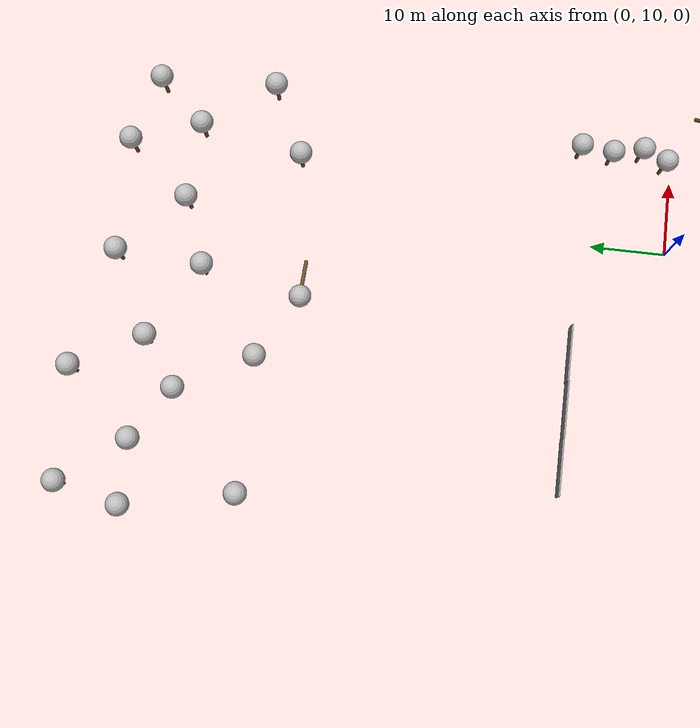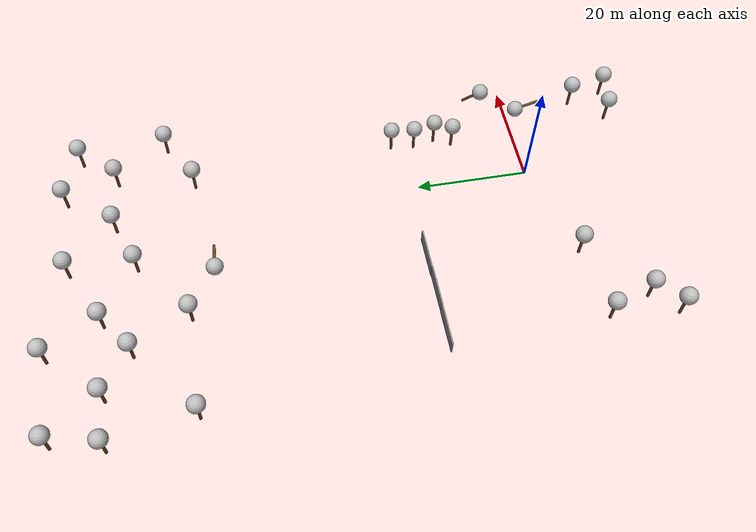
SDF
<sdf version="1.7">
 <world name="default">
  <plugin name="mrs_gazebo_static_transform_republisher_plugin" filename="libMrsGazeboCommonResources_StaticTransformRepublisher.so"/>
  <spherical_coordinates>
   <surface_model>EARTH_WGS84</surface_model>
   <latitude_deg>47.3977</latitude_deg>
   <longitude_deg>8.54559</longitude_deg>
   <elevation>0</elevation>
   <heading_deg>0</heading_deg>
  </spherical_coordinates>
  <physics name="default_physics" default="0" type="ode">
   <ode>
    <solver>
     <type>quick</type>
     <iters>10</iters>
     <sor>1.3</sor>
     <use_dynamic_moi_rescaling>0</use_dynamic_moi_rescaling>
    </solver>
    <constraints>
     <cfm>0</cfm>
     <erp>0.2</erp>
     <contact_max_correcting_vel>1000</contact_max_correcting_vel>
     <contact_surface_layer>0.001</contact_surface_layer>
    </constraints>
   </ode>
   <max_step_size>0.004</max_step_size>
   <real_time_factor>1</real_time_factor>
   <real_time_update_rate>250</real_time_update_rate>
  </physics>
  <scene><shadows>0</shadows><ambient>0.4 0.4 0.4 1</ambient><background>0.7 0.7 0.7 1</background></scene>
  <light name="sun" type="directional">
   <pose>0 0 1000 0.4 0.2 0</pose>
   <diffuse>1 1 1 1</diffuse>
   <specular>0.6 0.6 0.6 1</specular>
   <direction>0.1 0.1 -0.9</direction>
   <attenuation>
    <range>20</range>
    <constant>0.5</constant>
    <linear>0.01</linear>
    <quadratic>0.001</quadratic>
   </attenuation>
   <spot><inner_angle>0</inner_angle><outer_angle>0</outer_angle><falloff>0</falloff></spot>
  </light>
  <model name="the_void">
   <static>1</static>
   <link name="link">
    <pose>0 0 0.1 0 -0 0</pose>
    <visual name="the_void">
     <pose>0 0 2 0 -0 0</pose>
     <geometry><sphere><radius>0.25</radius></sphere></geometry>
     <material>
      <script><uri>file://media/materials/scripts/Gazebo.material</uri><name>Gazebo/Black</name></script>
     </material>
    </visual>
   </link>
   <pose>-1000 -1000 0 0 -0 0</pose>
  </model>
  <plugin name="mrs_gazebo_rviz_cam_synchronizer" filename="libMrsGazeboCommonResources_RvizCameraSynchronizer.so">
   <target_frame_id>gazebo_user_camera</target_frame_id>
   <world_origin_frame_id>uav1/gps_origin</world_origin_frame_id>
   <frame_to_follow>uav1</frame_to_follow>
  </plugin>
  <gravity>0 0 -9.8066</gravity>
  <magnetic_field>6e-06 2.3e-05 -4.2e-05</magnetic_field>
  <atmosphere type="adiabatic"/>
  <model name="tree_simple">
   <static>1</static>
   <link name="link">
    <pose>0 0 0.1 0 -0 0</pose>
    <inertial>
     <mass>666</mass>
     <inertia>
      <ixx>0.0861167</ixx>
      <ixy>0</ixy>
      <ixz>0</ixz>
      <iyy>0.0861167</iyy>
      <iyz>0</iyz>
      <izz>0.0861167</izz>
     </inertia>
    </inertial>
    <collision name="collision_trunk">
     <pose>0 0 2 0 -0 0</pose>
     <geometry><cylinder><radius>0.25</radius><length>4</length></cylinder></geometry>
     <surface>
      <contact>
       <poissons_ratio>0.347</poissons_ratio>
       <elastic_modulus>8.8e+09</elastic_modulus>
       <ode><kp>100000</kp><kd>100</kd><max_vel>100</max_vel><min_depth>0.001</min_depth></ode>
      </contact>
      <friction>
       <torsional>
        <coefficient>1</coefficient>
        <use_patch_radius>0</use_patch_radius>
        <surface_radius>0.01</surface_radius>
       </torsional>
      </friction>
     </surface>
    </collision>
    <collision name="collision_treetop">
     <pose>0 0 5.2 0 -0 0</pose>
     <geometry><sphere><radius>1.5</radius></sphere></geometry>
     <surface>
      <contact>
       <poissons_ratio>0.347</poissons_ratio>
       <elastic_modulus>8.8e+09</elastic_modulus>
       <ode><kp>100000</kp><kd>100</kd><max_vel>100</max_vel><min_depth>0.001</min_depth></ode>
      </contact>
      <friction>
       <torsional>
        <coefficient>1</coefficient>
        <use_patch_radius>0</use_patch_radius>
        <surface_radius>0.01</surface_radius>
       </torsional>
      </friction>
     </surface>
    </collision>
    <visual name="trunk">
     <pose>0 0 2 0 -0 0</pose>
     <geometry><cylinder><radius>0.25</radius><length>4</length></cylinder></geometry>
     <material>
      <script>
       <uri>model://tree_simple/scripts</uri>
       <uri>model://tree_simple/materials/textures</uri>
       <name>TreeSimple/Trunk</name>
      </script>
     </material>
    </visual>
    <visual name="treetop">
     <pose>0 0 5.2 0 -0 0</pose>
     <geometry><sphere><radius>1.5</radius></sphere></geometry>
     <material>
      <script>
       <uri>model://tree_simple/scripts</uri>
       <uri>model://tree_simple/materials/textures</uri>
       <name>TreeSimple/Treetop</name>
      </script>
     </material>
    </visual>
   </link>
   <pose>6.82311 59.8354 0 0 -0 0</pose>
  </model>
  <model name="tree_simple_0_clone_0">
   <static>1</static>
   <link name="link">
    <pose>0 0 0.1 0 -0 0</pose>
    <inertial>
     <mass>666</mass>
     <inertia>
      <ixx>0.0861167</ixx>
      <ixy>0</ixy>
      <ixz>0</ixz>
      <iyy>0.0861167</iyy>
      <iyz>0</iyz>
      <izz>0.0861167</izz>
     </inertia>
    </inertial>
    <collision name="collision_trunk">
     <pose>0 0 2 0 -0 0</pose>
     <geometry><cylinder><radius>0.25</radius><length>4</length></cylinder></geometry>
     <surface>
      <contact>
       <poissons_ratio>0.347</poissons_ratio>
       <elastic_modulus>8.8e+09</elastic_modulus>
       <ode><kp>100000</kp><kd>100</kd><max_vel>100</max_vel><min_depth>0.001</min_depth></ode>
      </contact>
      <friction>
       <torsional>
        <coefficient>1</coefficient>
        <use_patch_radius>0</use_patch_radius>
        <surface_radius>0.01</surface_radius>
       </torsional>
      </friction>
     </surface>
    </collision>
    <collision name="collision_treetop">
     <pose>0 0 5.2 0 -0 0</pose>
     <geometry><sphere><radius>1.5</radius></sphere></geometry>
     <surface>
      <contact>
       <poissons_ratio>0.347</poissons_ratio>
       <elastic_modulus>8.8e+09</elastic_modulus>
       <ode><kp>100000</kp><kd>100</kd><max_vel>100</max_vel><min_depth>0.001</min_depth></ode>
      </contact>
      <friction>
       <torsional>
        <coefficient>1</coefficient>
        <use_patch_radius>0</use_patch_radius>
        <surface_radius>0.01</surface_radius>
       </torsional>
      </friction>
     </surface>
    </collision>
    <visual name="trunk">
     <pose>0 0 2 0 -0 0</pose>
     <geometry><cylinder><radius>0.25</radius><length>4</length></cylinder></geometry>
     <material>
      <script>
       <uri>model://tree_simple/scripts</uri>
       <uri>model://tree_simple/materials/textures</uri>
       <name>TreeSimple/Trunk</name>
      </script>
     </material>
    </visual>
    <visual name="treetop">
     <pose>0 0 5.2 0 -0 0</pose>
     <geometry><sphere><radius>1.5</radius></sphere></geometry>
     <material>
      <script>
       <uri>model://tree_simple/scripts</uri>
       <uri>model://tree_simple/materials/textures</uri>
       <name>TreeSimple/Treetop</name>
      </script>
     </material>
    </visual>
   </link>
   <pose>-26.1429 71.9417 0 0 -0 0</pose>
  </model>
  <model name="tree_simple_0_clone_0_clone_clone">
   <static>1</static>
   <link name="link">
    <pose>0 0 0.1 0 -0 0</pose>
    <inertial>
     <mass>666</mass>
     <inertia>
      <ixx>0.0861167</ixx>
      <ixy>0</ixy>
      <ixz>0</ixz>
      <iyy>0.0861167</iyy>
      <iyz>0</iyz>
      <izz>0.0861167</izz>
     </inertia>
    </inertial>
    <collision name="collision_trunk">
     <pose>0 0 2 0 -0 0</pose>
     <geometry><cylinder><radius>0.25</radius><length>4</length></cylinder></geometry>
     <surface>
      <contact>
       <poissons_ratio>0.347</poissons_ratio>
       <elastic_modulus>8.8e+09</elastic_modulus>
       <ode><kp>100000</kp><kd>100</kd><max_vel>100</max_vel><min_depth>0.001</min_depth></ode>
      </contact>
      <friction>
       <torsional>
        <coefficient>1</coefficient>
        <use_patch_radius>0</use_patch_radius>
        <surface_radius>0.01</surface_radius>
       </torsional>
      </friction>
     </surface>
    </collision>
    <collision name="collision_treetop">
     <pose>0 0 5.2 0 -0 0</pose>
     <geometry><sphere><radius>1.5</radius></sphere></geometry>
     <surface>
      <contact>
       <poissons_ratio>0.347</poissons_ratio>
       <elastic_modulus>8.8e+09</elastic_modulus>
       <ode><kp>100000</kp><kd>100</kd><max_vel>100</max_vel><min_depth>0.001</min_depth></ode>
      </contact>
      <friction>
       <torsional>
        <coefficient>1</coefficient>
        <use_patch_radius>0</use_patch_radius>
        <surface_radius>0.01</surface_radius>
       </torsional>
      </friction>
     </surface>
    </collision>
    <visual name="trunk">
     <pose>0 0 2 0 -0 0</pose>
     <geometry><cylinder><radius>0.25</radius><length>4</length></cylinder></geometry>
     <material>
      <script>
       <uri>model://tree_simple/scripts</uri>
       <uri>model://tree_simple/materials/textures</uri>
       <name>TreeSimple/Trunk</name>
      </script>
     </material>
    </visual>
    <visual name="treetop">
     <pose>0 0 5.2 0 -0 0</pose>
     <geometry><sphere><radius>1.5</radius></sphere></geometry>
     <material>
      <script>
       <uri>model://tree_simple/scripts</uri>
       <uri>model://tree_simple/materials/textures</uri>
       <name>TreeSimple/Treetop</name>
      </script>
     </material>
    </visual>
   </link>
   <pose>-38.4069 62.1845 0 0 -0 0</pose>
  </model>
  <model name="tree_simple_0_clone_0_clone_clone_0">
   <static>1</static>
   <link name="link">
    <pose>0 0 0.1 0 -0 0</pose>
    <inertial>
     <mass>666</mass>
     <inertia>
      <ixx>0.0861167</ixx>
      <ixy>0</ixy>
      <ixz>0</ixz>
      <iyy>0.0861167</iyy>
      <iyz>0</iyz>
      <izz>0.0861167</izz>
     </inertia>
    </inertial>
    <collision name="collision_trunk">
     <pose>0 0 2 0 -0 0</pose>
     <geometry><cylinder><radius>0.25</radius><length>4</length></cylinder></geometry>
     <surface>
      <contact>
       <poissons_ratio>0.347</poissons_ratio>
       <elastic_modulus>8.8e+09</elastic_modulus>
       <ode><kp>100000</kp><kd>100</kd><max_vel>100</max_vel><min_depth>0.001</min_depth></ode>
      </contact>
      <friction>
       <torsional>
        <coefficient>1</coefficient>
        <use_patch_radius>0</use_patch_radius>
        <surface_radius>0.01</surface_radius>
       </torsional>
      </friction>
     </surface>
    </collision>
    <collision name="collision_treetop">
     <pose>0 0 5.2 0 -0 0</pose>
     <geometry><sphere><radius>1.5</radius></sphere></geometry>
     <surface>
      <contact>
       <poissons_ratio>0.347</poissons_ratio>
       <elastic_modulus>8.8e+09</elastic_modulus>
       <ode><kp>100000</kp><kd>100</kd><max_vel>100</max_vel><min_depth>0.001</min_depth></ode>
      </contact>
      <friction>
       <torsional>
        <coefficient>1</coefficient>
        <use_patch_radius>0</use_patch_radius>
        <surface_radius>0.01</surface_radius>
       </torsional>
      </friction>
     </surface>
    </collision>
    <visual name="trunk">
     <pose>0 0 2 0 -0 0</pose>
     <geometry><cylinder><radius>0.25</radius><length>4</length></cylinder></geometry>
     <material>
      <script>
       <uri>model://tree_simple/scripts</uri>
       <uri>model://tree_simple/materials/textures</uri>
       <name>TreeSimple/Trunk</name>
      </script>
     </material>
    </visual>
    <visual name="treetop">
     <pose>0 0 5.2 0 -0 0</pose>
     <geometry><sphere><radius>1.5</radius></sphere></geometry>
     <material>
      <script>
       <uri>model://tree_simple/scripts</uri>
       <uri>model://tree_simple/materials/textures</uri>
       <name>TreeSimple/Treetop</name>
      </script>
     </material>
    </visual>
   </link>
   <pose>9.58213 73.4959 0 0 -0 0</pose>
  </model>
  <model name="tree_simple_0_clone_0_clone_clone_4">
   <static>1</static>
   <link name="link">
    <pose>0 0 0.1 0 -0 0</pose>
    <inertial>
     <mass>666</mass>
     <inertia>
      <ixx>0.0861167</ixx>
      <ixy>0</ixy>
      <ixz>0</ixz>
      <iyy>0.0861167</iyy>
      <iyz>0</iyz>
      <izz>0.0861167</izz>
     </inertia>
    </inertial>
    <collision name="collision_trunk">
     <pose>0 0 2 0 -0 0</pose>
     <geometry><cylinder><radius>0.25</radius><length>4</length></cylinder></geometry>
     <surface>
      <contact>
       <poissons_ratio>0.347</poissons_ratio>
       <elastic_modulus>8.8e+09</elastic_modulus>
       <ode><kp>100000</kp><kd>100</kd><max_vel>100</max_vel><min_depth>0.001</min_depth></ode>
      </contact>
      <friction>
       <torsional>
        <coefficient>1</coefficient>
        <use_patch_radius>0</use_patch_radius>
        <surface_radius>0.01</surface_radius>
       </torsional>
      </friction>
     </surface>
    </collision>
    <collision name="collision_treetop">
     <pose>0 0 5.2 0 -0 0</pose>
     <geometry><sphere><radius>1.5</radius></sphere></geometry>
     <surface>
      <contact>
       <poissons_ratio>0.347</poissons_ratio>
       <elastic_modulus>8.8e+09</elastic_modulus>
       <ode><kp>100000</kp><kd>100</kd><max_vel>100</max_vel><min_depth>0.001</min_depth></ode>
      </contact>
      <friction>
       <torsional>
        <coefficient>1</coefficient>
        <use_patch_radius>0</use_patch_radius>
        <surface_radius>0.01</surface_radius>
       </torsional>
      </friction>
     </surface>
    </collision>
    <visual name="trunk">
     <pose>0 0 2 0 -0 0</pose>
     <geometry><cylinder><radius>0.25</radius><length>4</length></cylinder></geometry>
     <material>
      <script>
       <uri>model://tree_simple/scripts</uri>
       <uri>model://tree_simple/materials/textures</uri>
       <name>TreeSimple/Trunk</name>
      </script>
     </material>
    </visual>
    <visual name="treetop">
     <pose>0 0 5.2 0 -0 0</pose>
     <geometry><sphere><radius>1.5</radius></sphere></geometry>
     <material>
      <script>
       <uri>model://tree_simple/scripts</uri>
       <uri>model://tree_simple/materials/textures</uri>
       <name>TreeSimple/Treetop</name>
      </script>
     </material>
    </visual>
   </link>
   <pose>15.2966 -12.9591 0 0 -0 0</pose>
  </model>
  <model name="tree_simple_0_clone_0_clone_clone_5">
   <static>1</static>
   <link name="link">
    <pose>0 0 0.1 0 -0 0</pose>
    <inertial>
     <mass>666</mass>
     <inertia>
      <ixx>0.0861167</ixx>
      <ixy>0</ixy>
      <ixz>0</ixz>
      <iyy>0.0861167</iyy>
      <iyz>0</iyz>
      <izz>0.0861167</izz>
     </inertia>
    </inertial>
    <collision name="collision_trunk">
     <pose>0 0 2 0 -0 0</pose>
     <geometry><cylinder><radius>0.25</radius><length>4</length></cylinder></geometry>
     <surface>
      <contact>
       <poissons_ratio>0.347</poissons_ratio>
       <elastic_modulus>8.8e+09</elastic_modulus>
       <ode><kp>100000</kp><kd>100</kd><max_vel>100</max_vel><min_depth>0.001</min_depth></ode>
      </contact>
      <friction>
       <torsional>
        <coefficient>1</coefficient>
        <use_patch_radius>0</use_patch_radius>
        <surface_radius>0.01</surface_radius>
       </torsional>
      </friction>
     </surface>
    </collision>
    <collision name="collision_treetop">
     <pose>0 0 5.2 0 -0 0</pose>
     <geometry><sphere><radius>1.5</radius></sphere></geometry>
     <surface>
      <contact>
       <poissons_ratio>0.347</poissons_ratio>
       <elastic_modulus>8.8e+09</elastic_modulus>
       <ode><kp>100000</kp><kd>100</kd><max_vel>100</max_vel><min_depth>0.001</min_depth></ode>
      </contact>
      <friction>
       <torsional>
        <coefficient>1</coefficient>
        <use_patch_radius>0</use_patch_radius>
        <surface_radius>0.01</surface_radius>
       </torsional>
      </friction>
     </surface>
    </collision>
    <visual name="trunk">
     <pose>0 0 2 0 -0 0</pose>
     <geometry><cylinder><radius>0.25</radius><length>4</length></cylinder></geometry>
     <material>
      <script>
       <uri>model://tree_simple/scripts</uri>
       <uri>model://tree_simple/materials/textures</uri>
       <name>TreeSimple/Trunk</name>
      </script>
     </material>
    </visual>
    <visual name="treetop">
     <pose>0 0 5.2 0 -0 0</pose>
     <geometry><sphere><radius>1.5</radius></sphere></geometry>
     <material>
      <script>
       <uri>model://tree_simple/scripts</uri>
       <uri>model://tree_simple/materials/textures</uri>
       <name>TreeSimple/Treetop</name>
      </script>
     </material>
    </visual>
   </link>
   <pose>10.4515 -18.6405 0 0 -0 0</pose>
  </model>
  <model name="tree_simple_0_clone_0_clone_clone_6">
   <static>1</static>
   <link name="link">
    <pose>0 0 0.1 0 -0 0</pose>
    <inertial>
     <mass>666</mass>
     <inertia>
      <ixx>0.0861167</ixx>
      <ixy>0</ixy>
      <ixz>0</ixz>
      <iyy>0.0861167</iyy>
      <iyz>0</iyz>
      <izz>0.0861167</izz>
     </inertia>
    </inertial>
    <collision name="collision_trunk">
     <pose>0 0 2 0 -0 0</pose>
     <geometry><cylinder><radius>0.25</radius><length>4</length></cylinder></geometry>
     <surface>
      <contact>
       <poissons_ratio>0.347</poissons_ratio>
       <elastic_modulus>8.8e+09</elastic_modulus>
       <ode><kp>100000</kp><kd>100</kd><max_vel>100</max_vel><min_depth>0.001</min_depth></ode>
      </contact>
      <friction>
       <torsional>
        <coefficient>1</coefficient>
        <use_patch_radius>0</use_patch_radius>
        <surface_radius>0.01</surface_radius>
       </torsional>
      </friction>
     </surface>
    </collision>
    <collision name="collision_treetop">
     <pose>0 0 5.2 0 -0 0</pose>
     <geometry><sphere><radius>1.5</radius></sphere></geometry>
     <surface>
      <contact>
       <poissons_ratio>0.347</poissons_ratio>
       <elastic_modulus>8.8e+09</elastic_modulus>
       <ode><kp>100000</kp><kd>100</kd><max_vel>100</max_vel><min_depth>0.001</min_depth></ode>
      </contact>
      <friction>
       <torsional>
        <coefficient>1</coefficient>
        <use_patch_radius>0</use_patch_radius>
        <surface_radius>0.01</surface_radius>
       </torsional>
      </friction>
     </surface>
    </collision>
    <visual name="trunk">
     <pose>0 0 2 0 -0 0</pose>
     <geometry><cylinder><radius>0.25</radius><length>4</length></cylinder></geometry>
     <material>
      <script>
       <uri>model://tree_simple/scripts</uri>
       <uri>model://tree_simple/materials/textures</uri>
       <name>TreeSimple/Trunk</name>
      </script>
     </material>
    </visual>
    <visual name="treetop">
     <pose>0 0 5.2 0 -0 0</pose>
     <geometry><sphere><radius>1.5</radius></sphere></geometry>
     <material>
      <script>
       <uri>model://tree_simple/scripts</uri>
       <uri>model://tree_simple/materials/textures</uri>
       <name>TreeSimple/Treetop</name>
      </script>
     </material>
    </visual>
   </link>
   <pose>16.9128 -19.7494 0 0 -0 0</pose>
  </model>
  <model name="tree_simple_0_clone_0_clone_clone_9">
   <static>1</static>
   <link name="link">
    <pose>0 0 0.1 0 -0 0</pose>
    <inertial>
     <mass>666</mass>
     <inertia>
      <ixx>0.0861167</ixx>
      <ixy>0</ixy>
      <ixz>0</ixz>
      <iyy>0.0861167</iyy>
      <iyz>0</iyz>
      <izz>0.0861167</izz>
     </inertia>
    </inertial>
    <collision name="collision_trunk">
     <pose>0 0 2 0 -0 0</pose>
     <geometry><cylinder><radius>0.25</radius><length>4</length></cylinder></geometry>
     <surface>
      <contact>
       <poissons_ratio>0.347</poissons_ratio>
       <elastic_modulus>8.8e+09</elastic_modulus>
       <ode><kp>100000</kp><kd>100</kd><max_vel>100</max_vel><min_depth>0.001</min_depth></ode>
      </contact>
      <friction>
       <torsional>
        <coefficient>1</coefficient>
        <use_patch_radius>0</use_patch_radius>
        <surface_radius>0.01</surface_radius>
       </torsional>
      </friction>
     </surface>
    </collision>
    <collision name="collision_treetop">
     <pose>0 0 5.2 0 -0 0</pose>
     <geometry><sphere><radius>1.5</radius></sphere></geometry>
     <surface>
      <contact>
       <poissons_ratio>0.347</poissons_ratio>
       <elastic_modulus>8.8e+09</elastic_modulus>
       <ode><kp>100000</kp><kd>100</kd><max_vel>100</max_vel><min_depth>0.001</min_depth></ode>
      </contact>
      <friction>
       <torsional>
        <coefficient>1</coefficient>
        <use_patch_radius>0</use_patch_radius>
        <surface_radius>0.01</surface_radius>
       </torsional>
      </friction>
     </surface>
    </collision>
    <visual name="trunk">
     <pose>0 0 2 0 -0 0</pose>
     <geometry><cylinder><radius>0.25</radius><length>4</length></cylinder></geometry>
     <material>
      <script>
       <uri>model://tree_simple/scripts</uri>
       <uri>model://tree_simple/materials/textures</uri>
       <name>TreeSimple/Trunk</name>
      </script>
     </material>
    </visual>
    <visual name="treetop">
     <pose>0 0 5.2 0 -0 0</pose>
     <geometry><sphere><radius>1.5</radius></sphere></geometry>
     <material>
      <script>
       <uri>model://tree_simple/scripts</uri>
       <uri>model://tree_simple/materials/textures</uri>
       <name>TreeSimple/Treetop</name>
      </script>
     </material>
    </visual>
   </link>
   <pose>-0.789798 74.0707 0 0 -0 0</pose>
  </model>
  <model name="tree_simple_0_clone_0_clone_clone_10">
   <static>1</static>
   <link name="link">
    <pose>0 0 0.1 0 -0 0</pose>
    <inertial>
     <mass>666</mass>
     <inertia>
      <ixx>0.0861167</ixx>
      <ixy>0</ixy>
      <ixz>0</ixz>
      <iyy>0.0861167</iyy>
      <iyz>0</iyz>
      <izz>0.0861167</izz>
     </inertia>
    </inertial>
    <collision name="collision_trunk">
     <pose>0 0 2 0 -0 0</pose>
     <geometry><cylinder><radius>0.25</radius><length>4</length></cylinder></geometry>
     <surface>
      <contact>
       <poissons_ratio>0.347</poissons_ratio>
       <elastic_modulus>8.8e+09</elastic_modulus>
       <ode><kp>100000</kp><kd>100</kd><max_vel>100</max_vel><min_depth>0.001</min_depth></ode>
      </contact>
      <friction>
       <torsional>
        <coefficient>1</coefficient>
        <use_patch_radius>0</use_patch_radius>
        <surface_radius>0.01</surface_radius>
       </torsional>
      </friction>
     </surface>
    </collision>
    <collision name="collision_treetop">
     <pose>0 0 5.2 0 -0 0</pose>
     <geometry><sphere><radius>1.5</radius></sphere></geometry>
     <surface>
      <contact>
       <poissons_ratio>0.347</poissons_ratio>
       <elastic_modulus>8.8e+09</elastic_modulus>
       <ode><kp>100000</kp><kd>100</kd><max_vel>100</max_vel><min_depth>0.001</min_depth></ode>
      </contact>
      <friction>
       <torsional>
        <coefficient>1</coefficient>
        <use_patch_radius>0</use_patch_radius>
        <surface_radius>0.01</surface_radius>
       </torsional>
      </friction>
     </surface>
    </collision>
    <visual name="trunk">
     <pose>0 0 2 0 -0 0</pose>
     <geometry><cylinder><radius>0.25</radius><length>4</length></cylinder></geometry>
     <material>
      <script>
       <uri>model://tree_simple/scripts</uri>
       <uri>model://tree_simple/materials/textures</uri>
       <name>TreeSimple/Trunk</name>
      </script>
     </material>
    </visual>
    <visual name="treetop">
     <pose>0 0 5.2 0 -0 0</pose>
     <geometry><sphere><radius>1.5</radius></sphere></geometry>
     <material>
      <script>
       <uri>model://tree_simple/scripts</uri>
       <uri>model://tree_simple/materials/textures</uri>
       <name>TreeSimple/Treetop</name>
      </script>
     </material>
    </visual>
   </link>
   <pose>-33.1642 76.5434 0 0 -0 0</pose>
  </model>
  <model name="tree_simple_0_clone_0_clone_clone_11">
   <static>1</static>
   <link name="link">
    <pose>0 0 0.1 0 -0 0</pose>
    <inertial>
     <mass>666</mass>
     <inertia>
      <ixx>0.0861167</ixx>
      <ixy>0</ixy>
      <ixz>0</ixz>
      <iyy>0.0861167</iyy>
      <iyz>0</iyz>
      <izz>0.0861167</izz>
     </inertia>
    </inertial>
    <collision name="collision_trunk">
     <pose>0 0 2 0 -0 0</pose>
     <geometry><cylinder><radius>0.25</radius><length>4</length></cylinder></geometry>
     <surface>
      <contact>
       <poissons_ratio>0.347</poissons_ratio>
       <elastic_modulus>8.8e+09</elastic_modulus>
       <ode><kp>100000</kp><kd>100</kd><max_vel>100</max_vel><min_depth>0.001</min_depth></ode>
      </contact>
      <friction>
       <torsional>
        <coefficient>1</coefficient>
        <use_patch_radius>0</use_patch_radius>
        <surface_radius>0.01</surface_radius>
       </torsional>
      </friction>
     </surface>
    </collision>
    <collision name="collision_treetop">
     <pose>0 0 5.2 0 -0 0</pose>
     <geometry><sphere><radius>1.5</radius></sphere></geometry>
     <surface>
      <contact>
       <poissons_ratio>0.347</poissons_ratio>
       <elastic_modulus>8.8e+09</elastic_modulus>
       <ode><kp>100000</kp><kd>100</kd><max_vel>100</max_vel><min_depth>0.001</min_depth></ode>
      </contact>
      <friction>
       <torsional>
        <coefficient>1</coefficient>
        <use_patch_radius>0</use_patch_radius>
        <surface_radius>0.01</surface_radius>
       </torsional>
      </friction>
     </surface>
    </collision>
    <visual name="trunk">
     <pose>0 0 2 0 -0 0</pose>
     <geometry><cylinder><radius>0.25</radius><length>4</length></cylinder></geometry>
     <material>
      <script>
       <uri>model://tree_simple/scripts</uri>
       <uri>model://tree_simple/materials/textures</uri>
       <name>TreeSimple/Trunk</name>
      </script>
     </material>
    </visual>
    <visual name="treetop">
     <pose>0 0 5.2 0 -0 0</pose>
     <geometry><sphere><radius>1.5</radius></sphere></geometry>
     <material>
      <script>
       <uri>model://tree_simple/scripts</uri>
       <uri>model://tree_simple/materials/textures</uri>
       <name>TreeSimple/Treetop</name>
      </script>
     </material>
    </visual>
   </link>
   <pose>-19.78 76.5403 0 0 -0 0</pose>
  </model>
  <model name="tree_simple_0_clone_0_clone_clone_11_clone_0">
   <static>1</static>
   <link name="link">
    <pose>0 0 0.1 0 -0 0</pose>
    <inertial>
     <mass>666</mass>
     <inertia>
      <ixx>0.0861167</ixx>
      <ixy>0</ixy>
      <ixz>0</ixz>
      <iyy>0.0861167</iyy>
      <iyz>0</iyz>
      <izz>0.0861167</izz>
     </inertia>
    </inertial>
    <collision name="collision_trunk">
     <pose>0 0 2 0 -0 0</pose>
     <geometry><cylinder><radius>0.25</radius><length>4</length></cylinder></geometry>
     <surface>
      <contact>
       <poissons_ratio>0.347</poissons_ratio>
       <elastic_modulus>8.8e+09</elastic_modulus>
       <ode><kp>100000</kp><kd>100</kd><max_vel>100</max_vel><min_depth>0.001</min_depth></ode>
      </contact>
      <friction>
       <torsional>
        <coefficient>1</coefficient>
        <use_patch_radius>0</use_patch_radius>
        <surface_radius>0.01</surface_radius>
       </torsional>
      </friction>
     </surface>
    </collision>
    <collision name="collision_treetop">
     <pose>0 0 5.2 0 -0 0</pose>
     <geometry><sphere><radius>1.5</radius></sphere></geometry>
     <surface>
      <contact>
       <poissons_ratio>0.347</poissons_ratio>
       <elastic_modulus>8.8e+09</elastic_modulus>
       <ode><kp>100000</kp><kd>100</kd><max_vel>100</max_vel><min_depth>0.001</min_depth></ode>
      </contact>
      <friction>
       <torsional>
        <coefficient>1</coefficient>
        <use_patch_radius>0</use_patch_radius>
        <surface_radius>0.01</surface_radius>
       </torsional>
      </friction>
     </surface>
    </collision>
    <visual name="trunk">
     <pose>0 0 2 0 -0 0</pose>
     <geometry><cylinder><radius>0.25</radius><length>4</length></cylinder></geometry>
     <material>
      <script>
       <uri>model://tree_simple/scripts</uri>
       <uri>model://tree_simple/materials/textures</uri>
       <name>TreeSimple/Trunk</name>
      </script>
     </material>
    </visual>
    <visual name="treetop">
     <pose>0 0 5.2 0 -0 0</pose>
     <geometry><sphere><radius>1.5</radius></sphere></geometry>
     <material>
      <script>
       <uri>model://tree_simple/scripts</uri>
       <uri>model://tree_simple/materials/textures</uri>
       <name>TreeSimple/Treetop</name>
      </script>
     </material>
    </visual>
   </link>
   <pose>-41.4475 76.4622 0 0 -0 0</pose>
  </model>
  <model name="tree_simple_0_clone_0_clone_clone_11_clone_1">
   <static>1</static>
   <link name="link">
    <pose>0 0 0.1 0 -0 0</pose>
    <inertial>
     <mass>666</mass>
     <inertia>
      <ixx>0.0861167</ixx>
      <ixy>0</ixy>
      <ixz>0</ixz>
      <iyy>0.0861167</iyy>
      <iyz>0</iyz>
      <izz>0.0861167</izz>
     </inertia>
    </inertial>
    <collision name="collision_trunk">
     <pose>0 0 2 0 -0 0</pose>
     <geometry><cylinder><radius>0.25</radius><length>4</length></cylinder></geometry>
     <surface>
      <contact>
       <poissons_ratio>0.347</poissons_ratio>
       <elastic_modulus>8.8e+09</elastic_modulus>
       <ode><kp>100000</kp><kd>100</kd><max_vel>100</max_vel><min_depth>0.001</min_depth></ode>
      </contact>
      <friction>
       <torsional>
        <coefficient>1</coefficient>
        <use_patch_radius>0</use_patch_radius>
        <surface_radius>0.01</surface_radius>
       </torsional>
      </friction>
     </surface>
    </collision>
    <collision name="collision_treetop">
     <pose>0 0 5.2 0 -0 0</pose>
     <geometry><sphere><radius>1.5</radius></sphere></geometry>
     <surface>
      <contact>
       <poissons_ratio>0.347</poissons_ratio>
       <elastic_modulus>8.8e+09</elastic_modulus>
       <ode><kp>100000</kp><kd>100</kd><max_vel>100</max_vel><min_depth>0.001</min_depth></ode>
      </contact>
      <friction>
       <torsional>
        <coefficient>1</coefficient>
        <use_patch_radius>0</use_patch_radius>
        <surface_radius>0.01</surface_radius>
       </torsional>
      </friction>
     </surface>
    </collision>
    <visual name="trunk">
     <pose>0 0 2 0 -0 0</pose>
     <geometry><cylinder><radius>0.25</radius><length>4</length></cylinder></geometry>
     <material>
      <script>
       <uri>model://tree_simple/scripts</uri>
       <uri>model://tree_simple/materials/textures</uri>
       <name>TreeSimple/Trunk</name>
      </script>
     </material>
    </visual>
    <visual name="treetop">
     <pose>0 0 5.2 0 -0 0</pose>
     <geometry><sphere><radius>1.5</radius></sphere></geometry>
     <material>
      <script>
       <uri>model://tree_simple/scripts</uri>
       <uri>model://tree_simple/materials/textures</uri>
       <name>TreeSimple/Treetop</name>
      </script>
     </material>
    </visual>
   </link>
   <pose>6.31212 82.5438 0 0 -0 0</pose>
  </model>
  <model name="tree_simple_0_clone_0_clone_clone_11_clone_2">
   <static>1</static>
   <link name="link">
    <pose>0 0 0.1 0 -0 0</pose>
    <inertial>
     <mass>666</mass>
     <inertia>
      <ixx>0.0861167</ixx>
      <ixy>0</ixy>
      <ixz>0</ixz>
      <iyy>0.0861167</iyy>
      <iyz>0</iyz>
      <izz>0.0861167</izz>
     </inertia>
    </inertial>
    <collision name="collision_trunk">
     <pose>0 0 2 0 -0 0</pose>
     <geometry><cylinder><radius>0.25</radius><length>4</length></cylinder></geometry>
     <surface>
      <contact>
       <poissons_ratio>0.347</poissons_ratio>
       <elastic_modulus>8.8e+09</elastic_modulus>
       <ode><kp>100000</kp><kd>100</kd><max_vel>100</max_vel><min_depth>0.001</min_depth></ode>
      </contact>
      <friction>
       <torsional>
        <coefficient>1</coefficient>
        <use_patch_radius>0</use_patch_radius>
        <surface_radius>0.01</surface_radius>
       </torsional>
      </friction>
     </surface>
    </collision>
    <collision name="collision_treetop">
     <pose>0 0 5.2 0 -0 0</pose>
     <geometry><sphere><radius>1.5</radius></sphere></geometry>
     <surface>
      <contact>
       <poissons_ratio>0.347</poissons_ratio>
       <elastic_modulus>8.8e+09</elastic_modulus>
       <ode><kp>100000</kp><kd>100</kd><max_vel>100</max_vel><min_depth>0.001</min_depth></ode>
      </contact>
      <friction>
       <torsional>
        <coefficient>1</coefficient>
        <use_patch_radius>0</use_patch_radius>
        <surface_radius>0.01</surface_radius>
       </torsional>
      </friction>
     </surface>
    </collision>
    <visual name="trunk">
     <pose>0 0 2 0 -0 0</pose>
     <geometry><cylinder><radius>0.25</radius><length>4</length></cylinder></geometry>
     <material>
      <script>
       <uri>model://tree_simple/scripts</uri>
       <uri>model://tree_simple/materials/textures</uri>
       <name>TreeSimple/Trunk</name>
      </script>
     </material>
    </visual>
    <visual name="treetop">
     <pose>0 0 5.2 0 -0 0</pose>
     <geometry><sphere><radius>1.5</radius></sphere></geometry>
     <material>
      <script>
       <uri>model://tree_simple/scripts</uri>
       <uri>model://tree_simple/materials/textures</uri>
       <name>TreeSimple/Treetop</name>
      </script>
     </material>
    </visual>
   </link>
   <pose>15.4317 79.7817 0 0 -0 0</pose>
  </model>
  <model name="tree_simple_0_clone_0_clone_clone_1_clone_clone_1">
   <static>1</static>
   <link name="link">
    <pose>0 0 0.1 0 -0 0</pose>
    <inertial>
     <mass>666</mass>
     <inertia>
      <ixx>0.0861167</ixx>
      <ixy>0</ixy>
      <ixz>0</ixz>
      <iyy>0.0861167</iyy>
      <iyz>0</iyz>
      <izz>0.0861167</izz>
     </inertia>
    </inertial>
    <collision name="collision_trunk">
     <pose>0 0 2 0 -0 0</pose>
     <geometry><cylinder><radius>0.25</radius><length>4</length></cylinder></geometry>
     <surface>
      <contact>
       <poissons_ratio>0.347</poissons_ratio>
       <elastic_modulus>8.8e+09</elastic_modulus>
       <ode><kp>100000</kp><kd>100</kd><max_vel>100</max_vel><min_depth>0.001</min_depth></ode>
      </contact>
      <friction>
       <torsional>
        <coefficient>1</coefficient>
        <use_patch_radius>0</use_patch_radius>
        <surface_radius>0.01</surface_radius>
       </torsional>
      </friction>
     </surface>
    </collision>
    <collision name="collision_treetop">
     <pose>0 0 5.2 0 -0 0</pose>
     <geometry><sphere><radius>1.5</radius></sphere></geometry>
     <surface>
      <contact>
       <poissons_ratio>0.347</poissons_ratio>
       <elastic_modulus>8.8e+09</elastic_modulus>
       <ode><kp>100000</kp><kd>100</kd><max_vel>100</max_vel><min_depth>0.001</min_depth></ode>
      </contact>
      <friction>
       <torsional>
        <coefficient>1</coefficient>
        <use_patch_radius>0</use_patch_radius>
        <surface_radius>0.01</surface_radius>
       </torsional>
      </friction>
     </surface>
    </collision>
    <visual name="trunk">
     <pose>0 0 2 0 -0 0</pose>
     <geometry><cylinder><radius>0.25</radius><length>4</length></cylinder></geometry>
     <material>
      <script>
       <uri>model://tree_simple/scripts</uri>
       <uri>model://tree_simple/materials/textures</uri>
       <name>TreeSimple/Trunk</name>
      </script>
     </material>
    </visual>
    <visual name="treetop">
     <pose>0 0 5.2 0 -0 0</pose>
     <geometry><sphere><radius>1.5</radius></sphere></geometry>
     <material>
      <script>
       <uri>model://tree_simple/scripts</uri>
       <uri>model://tree_simple/materials/textures</uri>
       <name>TreeSimple/Treetop</name>
      </script>
     </material>
    </visual>
   </link>
   <pose>14.4798 22.0908 -5.25636 0 -0 0</pose>
  </model>
  <model name="tree_simple_0_clone_0_clone_clone_1_clone_clone_2">
   <static>1</static>
   <link name="link">
    <pose>0 0 0.1 0 -0 0</pose>
    <inertial>
     <mass>666</mass>
     <inertia>
      <ixx>0.0861167</ixx>
      <ixy>0</ixy>
      <ixz>0</ixz>
      <iyy>0.0861167</iyy>
      <iyz>0</iyz>
      <izz>0.0861167</izz>
     </inertia>
    </inertial>
    <collision name="collision_trunk">
     <pose>0 0 2 0 -0 0</pose>
     <geometry><cylinder><radius>0.25</radius><length>4</length></cylinder></geometry>
     <surface>
      <contact>
       <poissons_ratio>0.347</poissons_ratio>
       <elastic_modulus>8.8e+09</elastic_modulus>
       <ode><kp>100000</kp><kd>100</kd><max_vel>100</max_vel><min_depth>0.001</min_depth></ode>
      </contact>
      <friction>
       <torsional>
        <coefficient>1</coefficient>
        <use_patch_radius>0</use_patch_radius>
        <surface_radius>0.01</surface_radius>
       </torsional>
      </friction>
     </surface>
    </collision>
    <collision name="collision_treetop">
     <pose>0 0 5.2 0 -0 0</pose>
     <geometry><sphere><radius>1.5</radius></sphere></geometry>
     <surface>
      <contact>
       <poissons_ratio>0.347</poissons_ratio>
       <elastic_modulus>8.8e+09</elastic_modulus>
       <ode><kp>100000</kp><kd>100</kd><max_vel>100</max_vel><min_depth>0.001</min_depth></ode>
      </contact>
      <friction>
       <torsional>
        <coefficient>1</coefficient>
        <use_patch_radius>0</use_patch_radius>
        <surface_radius>0.01</surface_radius>
       </torsional>
      </friction>
     </surface>
    </collision>
    <visual name="trunk">
     <pose>0 0 2 0 -0 0</pose>
     <geometry><cylinder><radius>0.25</radius><length>4</length></cylinder></geometry>
     <material>
      <script>
       <uri>model://tree_simple/scripts</uri>
       <uri>model://tree_simple/materials/textures</uri>
       <name>TreeSimple/Trunk</name>
      </script>
     </material>
    </visual>
    <visual name="treetop">
     <pose>0 0 5.2 0 -0 0</pose>
     <geometry><sphere><radius>1.5</radius></sphere></geometry>
     <material>
      <script>
       <uri>model://tree_simple/scripts</uri>
       <uri>model://tree_simple/materials/textures</uri>
       <name>TreeSimple/Treetop</name>
      </script>
     </material>
    </visual>
   </link>
   <pose>13.9771 17.7579 -5.17122 0 -0 0</pose>
  </model>
  <model name="tree_simple_0_clone_0_clone_clone_1_clone_clone_4">
   <static>1</static>
   <link name="link">
    <pose>0 0 0.1 0 -0 0</pose>
    <inertial>
     <mass>666</mass>
     <inertia>
      <ixx>0.0861167</ixx>
      <ixy>0</ixy>
      <ixz>0</ixz>
      <iyy>0.0861167</iyy>
      <iyz>0</iyz>
      <izz>0.0861167</izz>
     </inertia>
    </inertial>
    <collision name="collision_trunk">
     <pose>0 0 2 0 -0 0</pose>
     <geometry><cylinder><radius>0.25</radius><length>4</length></cylinder></geometry>
     <surface>
      <contact>
       <poissons_ratio>0.347</poissons_ratio>
       <elastic_modulus>8.8e+09</elastic_modulus>
       <ode><kp>100000</kp><kd>100</kd><max_vel>100</max_vel><min_depth>0.001</min_depth></ode>
      </contact>
      <friction>
       <torsional>
        <coefficient>1</coefficient>
        <use_patch_radius>0</use_patch_radius>
        <surface_radius>0.01</surface_radius>
       </torsional>
      </friction>
     </surface>
    </collision>
    <collision name="collision_treetop">
     <pose>0 0 5.2 0 -0 0</pose>
     <geometry><sphere><radius>1.5</radius></sphere></geometry>
     <surface>
      <contact>
       <poissons_ratio>0.347</poissons_ratio>
       <elastic_modulus>8.8e+09</elastic_modulus>
       <ode><kp>100000</kp><kd>100</kd><max_vel>100</max_vel><min_depth>0.001</min_depth></ode>
      </contact>
      <friction>
       <torsional>
        <coefficient>1</coefficient>
        <use_patch_radius>0</use_patch_radius>
        <surface_radius>0.01</surface_radius>
       </torsional>
      </friction>
     </surface>
    </collision>
    <visual name="trunk">
     <pose>0 0 2 0 -0 0</pose>
     <geometry><cylinder><radius>0.25</radius><length>4</length></cylinder></geometry>
     <material>
      <script>
       <uri>model://tree_simple/scripts</uri>
       <uri>model://tree_simple/materials/textures</uri>
       <name>TreeSimple/Trunk</name>
      </script>
     </material>
    </visual>
    <visual name="treetop">
     <pose>0 0 5.2 0 -0 0</pose>
     <geometry><sphere><radius>1.5</radius></sphere></geometry>
     <material>
      <script>
       <uri>model://tree_simple/scripts</uri>
       <uri>model://tree_simple/materials/textures</uri>
       <name>TreeSimple/Treetop</name>
      </script>
     </material>
    </visual>
   </link>
   <pose>14.8506 13.6404 -5.11548 0 -0 0</pose>
  </model>
  <model name="tree_simple_0_clone_0_clone_clone_1_clone_clone_5">
   <static>1</static>
   <link name="link">
    <pose>0 0 0.1 0 -0 0</pose>
    <inertial>
     <mass>666</mass>
     <inertia>
      <ixx>0.0861167</ixx>
      <ixy>0</ixy>
      <ixz>0</ixz>
      <iyy>0.0861167</iyy>
      <iyz>0</iyz>
      <izz>0.0861167</izz>
     </inertia>
    </inertial>
    <collision name="collision_trunk">
     <pose>0 0 2 0 -0 0</pose>
     <geometry><cylinder><radius>0.25</radius><length>4</length></cylinder></geometry>
     <surface>
      <contact>
       <poissons_ratio>0.347</poissons_ratio>
       <elastic_modulus>8.8e+09</elastic_modulus>
       <ode><kp>100000</kp><kd>100</kd><max_vel>100</max_vel><min_depth>0.001</min_depth></ode>
      </contact>
      <friction>
       <torsional>
        <coefficient>1</coefficient>
        <use_patch_radius>0</use_patch_radius>
        <surface_radius>0.01</surface_radius>
       </torsional>
      </friction>
     </surface>
    </collision>
    <collision name="collision_treetop">
     <pose>0 0 5.2 0 -0 0</pose>
     <geometry><sphere><radius>1.5</radius></sphere></geometry>
     <surface>
      <contact>
       <poissons_ratio>0.347</poissons_ratio>
       <elastic_modulus>8.8e+09</elastic_modulus>
       <ode><kp>100000</kp><kd>100</kd><max_vel>100</max_vel><min_depth>0.001</min_depth></ode>
      </contact>
      <friction>
       <torsional>
        <coefficient>1</coefficient>
        <use_patch_radius>0</use_patch_radius>
        <surface_radius>0.01</surface_radius>
       </torsional>
      </friction>
     </surface>
    </collision>
    <visual name="trunk">
     <pose>0 0 2 0 -0 0</pose>
     <geometry><cylinder><radius>0.25</radius><length>4</length></cylinder></geometry>
     <material>
      <script>
       <uri>model://tree_simple/scripts</uri>
       <uri>model://tree_simple/materials/textures</uri>
       <name>TreeSimple/Trunk</name>
      </script>
     </material>
    </visual>
    <visual name="treetop">
     <pose>0 0 5.2 0 -0 0</pose>
     <geometry><sphere><radius>1.5</radius></sphere></geometry>
     <material>
      <script>
       <uri>model://tree_simple/scripts</uri>
       <uri>model://tree_simple/materials/textures</uri>
       <name>TreeSimple/Treetop</name>
      </script>
     </material>
    </visual>
   </link>
   <pose>13.5534 10.354 -5.37186 0 -0 0</pose>
  </model>
  <model name="tree_simple_0_clone_0_clone_clone_4_clone_1">
   <static>1</static>
   <link name="link">
    <pose>0 0 0.1 0 -0 0</pose>
    <inertial>
     <mass>666</mass>
     <inertia>
      <ixx>0.0861167</ixx>
      <ixy>0</ixy>
      <ixz>0</ixz>
      <iyy>0.0861167</iyy>
      <iyz>0</iyz>
      <izz>0.0861167</izz>
     </inertia>
    </inertial>
    <collision name="collision_trunk">
     <pose>0 0 2 0 -0 0</pose>
     <geometry><cylinder><radius>0.25</radius><length>4</length></cylinder></geometry>
     <surface>
      <contact>
       <poissons_ratio>0.347</poissons_ratio>
       <elastic_modulus>8.8e+09</elastic_modulus>
       <ode><kp>100000</kp><kd>100</kd><max_vel>100</max_vel><min_depth>0.001</min_depth></ode>
      </contact>
      <friction>
       <torsional>
        <coefficient>1</coefficient>
        <use_patch_radius>0</use_patch_radius>
        <surface_radius>0.01</surface_radius>
       </torsional>
      </friction>
     </surface>
    </collision>
    <collision name="collision_treetop">
     <pose>0 0 5.2 0 -0 0</pose>
     <geometry><sphere><radius>1.5</radius></sphere></geometry>
     <surface>
      <contact>
       <poissons_ratio>0.347</poissons_ratio>
       <elastic_modulus>8.8e+09</elastic_modulus>
       <ode><kp>100000</kp><kd>100</kd><max_vel>100</max_vel><min_depth>0.001</min_depth></ode>
      </contact>
      <friction>
       <torsional>
        <coefficient>1</coefficient>
        <use_patch_radius>0</use_patch_radius>
        <surface_radius>0.01</surface_radius>
       </torsional>
      </friction>
     </surface>
    </collision>
    <visual name="trunk">
     <pose>0 0 2 0 -0 0</pose>
     <geometry><cylinder><radius>0.25</radius><length>4</length></cylinder></geometry>
     <material>
      <script>
       <uri>model://tree_simple/scripts</uri>
       <uri>model://tree_simple/materials/textures</uri>
       <name>TreeSimple/Trunk</name>
      </script>
     </material>
    </visual>
    <visual name="treetop">
     <pose>0 0 5.2 0 -0 0</pose>
     <geometry><sphere><radius>1.5</radius></sphere></geometry>
     <material>
      <script>
       <uri>model://tree_simple/scripts</uri>
       <uri>model://tree_simple/materials/textures</uri>
       <name>TreeSimple/Treetop</name>
      </script>
     </material>
    </visual>
   </link>
   <pose>19.8831 6.96556 0 0.512405 -0.508067 0</pose>
  </model>
  <model name="tree_simple_0_clone_0_clone_clone_4_clone_2">
   <static>1</static>
   <link name="link">
    <pose>0 0 0.1 0 -0 0</pose>
    <inertial>
     <mass>666</mass>
     <inertia>
      <ixx>0.0861167</ixx>
      <ixy>0</ixy>
      <ixz>0</ixz>
      <iyy>0.0861167</iyy>
      <iyz>0</iyz>
      <izz>0.0861167</izz>
     </inertia>
    </inertial>
    <collision name="collision_trunk">
     <pose>0 0 2 0 -0 0</pose>
     <geometry><cylinder><radius>0.25</radius><length>4</length></cylinder></geometry>
     <surface>
      <contact>
       <poissons_ratio>0.347</poissons_ratio>
       <elastic_modulus>8.8e+09</elastic_modulus>
       <ode><kp>100000</kp><kd>100</kd><max_vel>100</max_vel><min_depth>0.001</min_depth></ode>
      </contact>
      <friction>
       <torsional>
        <coefficient>1</coefficient>
        <use_patch_radius>0</use_patch_radius>
        <surface_radius>0.01</surface_radius>
       </torsional>
      </friction>
     </surface>
    </collision>
    <collision name="collision_treetop">
     <pose>0 0 5.2 0 -0 0</pose>
     <geometry><sphere><radius>1.5</radius></sphere></geometry>
     <surface>
      <contact>
       <poissons_ratio>0.347</poissons_ratio>
       <elastic_modulus>8.8e+09</elastic_modulus>
       <ode><kp>100000</kp><kd>100</kd><max_vel>100</max_vel><min_depth>0.001</min_depth></ode>
      </contact>
      <friction>
       <torsional>
        <coefficient>1</coefficient>
        <use_patch_radius>0</use_patch_radius>
        <surface_radius>0.01</surface_radius>
       </torsional>
      </friction>
     </surface>
    </collision>
    <visual name="trunk">
     <pose>0 0 2 0 -0 0</pose>
     <geometry><cylinder><radius>0.25</radius><length>4</length></cylinder></geometry>
     <material>
      <script>
       <uri>model://tree_simple/scripts</uri>
       <uri>model://tree_simple/materials/textures</uri>
       <name>TreeSimple/Trunk</name>
      </script>
     </material>
    </visual>
    <visual name="treetop">
     <pose>0 0 5.2 0 -0 0</pose>
     <geometry><sphere><radius>1.5</radius></sphere></geometry>
     <material>
      <script>
       <uri>model://tree_simple/scripts</uri>
       <uri>model://tree_simple/materials/textures</uri>
       <name>TreeSimple/Treetop</name>
      </script>
     </material>
    </visual>
   </link>
   <pose>17.1164 -7.53374 0 -1.26113 -1.33036 0</pose>
  </model>
  <model name="tree_simple_0_clone_0_clone_clone_clone_0">
   <static>1</static>
   <link name="link">
    <pose>0 0 0.1 0 -0 0</pose>
    <inertial>
     <mass>666</mass>
     <inertia>
      <ixx>0.0861167</ixx>
      <ixy>0</ixy>
      <ixz>0</ixz>
      <iyy>0.0861167</iyy>
      <iyz>0</iyz>
      <izz>0.0861167</izz>
     </inertia>
    </inertial>
    <collision name="collision_trunk">
     <pose>0 0 2 0 -0 0</pose>
     <geometry><cylinder><radius>0.25</radius><length>4</length></cylinder></geometry>
     <surface>
      <contact>
       <poissons_ratio>0.347</poissons_ratio>
       <elastic_modulus>8.8e+09</elastic_modulus>
       <ode><kp>100000</kp><kd>100</kd><max_vel>100</max_vel><min_depth>0.001</min_depth></ode>
      </contact>
      <friction>
       <torsional>
        <coefficient>1</coefficient>
        <use_patch_radius>0</use_patch_radius>
        <surface_radius>0.01</surface_radius>
       </torsional>
      </friction>
     </surface>
    </collision>
    <collision name="collision_treetop">
     <pose>0 0 5.2 0 -0 0</pose>
     <geometry><sphere><radius>1.5</radius></sphere></geometry>
     <surface>
      <contact>
       <poissons_ratio>0.347</poissons_ratio>
       <elastic_modulus>8.8e+09</elastic_modulus>
       <ode><kp>100000</kp><kd>100</kd><max_vel>100</max_vel><min_depth>0.001</min_depth></ode>
      </contact>
      <friction>
       <torsional>
        <coefficient>1</coefficient>
        <use_patch_radius>0</use_patch_radius>
        <surface_radius>0.01</surface_radius>
       </torsional>
      </friction>
     </surface>
    </collision>
    <visual name="trunk">
     <pose>0 0 2 0 -0 0</pose>
     <geometry><cylinder><radius>0.25</radius><length>4</length></cylinder></geometry>
     <material>
      <script>
       <uri>model://tree_simple/scripts</uri>
       <uri>model://tree_simple/materials/textures</uri>
       <name>TreeSimple/Trunk</name>
      </script>
     </material>
    </visual>
    <visual name="treetop">
     <pose>0 0 5.2 0 -0 0</pose>
     <geometry><sphere><radius>1.5</radius></sphere></geometry>
     <material>
      <script>
       <uri>model://tree_simple/scripts</uri>
       <uri>model://tree_simple/materials/textures</uri>
       <name>TreeSimple/Treetop</name>
      </script>
     </material>
    </visual>
   </link>
   <pose>-20.859 62.2392 0 0 -0 0</pose>
  </model>
  <model name="tree_simple_0_clone_0_clone_clone_clone_1">
   <static>1</static>
   <link name="link">
    <pose>0 0 0.1 0 -0 0</pose>
    <inertial>
     <mass>666</mass>
     <inertia>
      <ixx>0.0861167</ixx>
      <ixy>0</ixy>
      <ixz>0</ixz>
      <iyy>0.0861167</iyy>
      <iyz>0</iyz>
      <izz>0.0861167</izz>
     </inertia>
    </inertial>
    <collision name="collision_trunk">
     <pose>0 0 2 0 -0 0</pose>
     <geometry><cylinder><radius>0.25</radius><length>4</length></cylinder></geometry>
     <surface>
      <contact>
       <poissons_ratio>0.347</poissons_ratio>
       <elastic_modulus>8.8e+09</elastic_modulus>
       <ode><kp>100000</kp><kd>100</kd><max_vel>100</max_vel><min_depth>0.001</min_depth></ode>
      </contact>
      <friction>
       <torsional>
        <coefficient>1</coefficient>
        <use_patch_radius>0</use_patch_radius>
        <surface_radius>0.01</surface_radius>
       </torsional>
      </friction>
     </surface>
    </collision>
    <collision name="collision_treetop">
     <pose>0 0 5.2 0 -0 0</pose>
     <geometry><sphere><radius>1.5</radius></sphere></geometry>
     <surface>
      <contact>
       <poissons_ratio>0.347</poissons_ratio>
       <elastic_modulus>8.8e+09</elastic_modulus>
       <ode><kp>100000</kp><kd>100</kd><max_vel>100</max_vel><min_depth>0.001</min_depth></ode>
      </contact>
      <friction>
       <torsional>
        <coefficient>1</coefficient>
        <use_patch_radius>0</use_patch_radius>
        <surface_radius>0.01</surface_radius>
       </torsional>
      </friction>
     </surface>
    </collision>
    <visual name="trunk">
     <pose>0 0 2 0 -0 0</pose>
     <geometry><cylinder><radius>0.25</radius><length>4</length></cylinder></geometry>
     <material>
      <script>
       <uri>model://tree_simple/scripts</uri>
       <uri>model://tree_simple/materials/textures</uri>
       <name>TreeSimple/Trunk</name>
      </script>
     </material>
    </visual>
    <visual name="treetop">
     <pose>0 0 5.2 0 -0 0</pose>
     <geometry><sphere><radius>1.5</radius></sphere></geometry>
     <material>
      <script>
       <uri>model://tree_simple/scripts</uri>
       <uri>model://tree_simple/materials/textures</uri>
       <name>TreeSimple/Treetop</name>
      </script>
     </material>
    </visual>
   </link>
   <pose>-39.4409 84.8363 0 0 -0 0</pose>
  </model>
  <model name="tree_simple_0_clone_0_clone_clone_clone_0_clone">
   <static>1</static>
   <link name="link">
    <pose>0 0 0.1 0 -0 0</pose>
    <inertial>
     <mass>666</mass>
     <inertia>
      <ixx>0.0861167</ixx>
      <ixy>0</ixy>
      <ixz>0</ixz>
      <iyy>0.0861167</iyy>
      <iyz>0</iyz>
      <izz>0.0861167</izz>
     </inertia>
    </inertial>
    <collision name="collision_trunk">
     <pose>0 0 2 0 -0 0</pose>
     <geometry><cylinder><radius>0.25</radius><length>4</length></cylinder></geometry>
     <surface>
      <contact>
       <poissons_ratio>0.347</poissons_ratio>
       <elastic_modulus>8.8e+09</elastic_modulus>
       <ode><kp>100000</kp><kd>100</kd><max_vel>100</max_vel><min_depth>0.001</min_depth></ode>
      </contact>
      <friction>
       <torsional>
        <coefficient>1</coefficient>
        <use_patch_radius>0</use_patch_radius>
        <surface_radius>0.01</surface_radius>
       </torsional>
      </friction>
     </surface>
    </collision>
    <collision name="collision_treetop">
     <pose>0 0 5.2 0 -0 0</pose>
     <geometry><sphere><radius>1.5</radius></sphere></geometry>
     <surface>
      <contact>
       <poissons_ratio>0.347</poissons_ratio>
       <elastic_modulus>8.8e+09</elastic_modulus>
       <ode><kp>100000</kp><kd>100</kd><max_vel>100</max_vel><min_depth>0.001</min_depth></ode>
      </contact>
      <friction>
       <torsional>
        <coefficient>1</coefficient>
        <use_patch_radius>0</use_patch_radius>
        <surface_radius>0.01</surface_radius>
       </torsional>
      </friction>
     </surface>
    </collision>
    <visual name="trunk">
     <pose>0 0 2 0 -0 0</pose>
     <geometry><cylinder><radius>0.25</radius><length>4</length></cylinder></geometry>
     <material>
      <script>
       <uri>model://tree_simple/scripts</uri>
       <uri>model://tree_simple/materials/textures</uri>
       <name>TreeSimple/Trunk</name>
      </script>
     </material>
    </visual>
    <visual name="treetop">
     <pose>0 0 5.2 0 -0 0</pose>
     <geometry><sphere><radius>1.5</radius></sphere></geometry>
     <material>
      <script>
       <uri>model://tree_simple/scripts</uri>
       <uri>model://tree_simple/materials/textures</uri>
       <name>TreeSimple/Treetop</name>
      </script>
     </material>
    </visual>
   </link>
   <pose>-24.768 85.6073 0 0 -0 0</pose>
  </model>
  <model name="tree_simple_0_clone_0_clone_clone_clone_0_clone_0">
   <static>1</static>
   <link name="link">
    <pose>0 0 0.1 0 -0 0</pose>
    <inertial>
     <mass>666</mass>
     <inertia>
      <ixx>0.0861167</ixx>
      <ixy>0</ixy>
      <ixz>0</ixz>
      <iyy>0.0861167</iyy>
      <iyz>0</iyz>
      <izz>0.0861167</izz>
     </inertia>
    </inertial>
    <collision name="collision_trunk">
     <pose>0 0 2 0 -0 0</pose>
     <geometry><cylinder><radius>0.25</radius><length>4</length></cylinder></geometry>
     <surface>
      <contact>
       <poissons_ratio>0.347</poissons_ratio>
       <elastic_modulus>8.8e+09</elastic_modulus>
       <ode><kp>100000</kp><kd>100</kd><max_vel>100</max_vel><min_depth>0.001</min_depth></ode>
      </contact>
      <friction>
       <torsional>
        <coefficient>1</coefficient>
        <use_patch_radius>0</use_patch_radius>
        <surface_radius>0.01</surface_radius>
       </torsional>
      </friction>
     </surface>
    </collision>
    <collision name="collision_treetop">
     <pose>0 0 5.2 0 -0 0</pose>
     <geometry><sphere><radius>1.5</radius></sphere></geometry>
     <surface>
      <contact>
       <poissons_ratio>0.347</poissons_ratio>
       <elastic_modulus>8.8e+09</elastic_modulus>
       <ode><kp>100000</kp><kd>100</kd><max_vel>100</max_vel><min_depth>0.001</min_depth></ode>
      </contact>
      <friction>
       <torsional>
        <coefficient>1</coefficient>
        <use_patch_radius>0</use_patch_radius>
        <surface_radius>0.01</surface_radius>
       </torsional>
      </friction>
     </surface>
    </collision>
    <visual name="trunk">
     <pose>0 0 2 0 -0 0</pose>
     <geometry><cylinder><radius>0.25</radius><length>4</length></cylinder></geometry>
     <material>
      <script>
       <uri>model://tree_simple/scripts</uri>
       <uri>model://tree_simple/materials/textures</uri>
       <name>TreeSimple/Trunk</name>
      </script>
     </material>
    </visual>
    <visual name="treetop">
     <pose>0 0 5.2 0 -0 0</pose>
     <geometry><sphere><radius>1.5</radius></sphere></geometry>
     <material>
      <script>
       <uri>model://tree_simple/scripts</uri>
       <uri>model://tree_simple/materials/textures</uri>
       <name>TreeSimple/Treetop</name>
      </script>
     </material>
    </visual>
   </link>
   <pose>-8.94884 82.1007 0 0 -0 0</pose>
  </model>
  <model name="tree_simple_0_clone_0_clone_clone_clone_0_clone_1">
   <static>1</static>
   <link name="link">
    <pose>0 0 0.1 0 -0 0</pose>
    <inertial>
     <mass>666</mass>
     <inertia>
      <ixx>0.0861167</ixx>
      <ixy>0</ixy>
      <ixz>0</ixz>
      <iyy>0.0861167</iyy>
      <iyz>0</iyz>
      <izz>0.0861167</izz>
     </inertia>
    </inertial>
    <collision name="collision_trunk">
     <pose>0 0 2 0 -0 0</pose>
     <geometry><cylinder><radius>0.25</radius><length>4</length></cylinder></geometry>
     <surface>
      <contact>
       <poissons_ratio>0.347</poissons_ratio>
       <elastic_modulus>8.8e+09</elastic_modulus>
       <ode><kp>100000</kp><kd>100</kd><max_vel>100</max_vel><min_depth>0.001</min_depth></ode>
      </contact>
      <friction>
       <torsional>
        <coefficient>1</coefficient>
        <use_patch_radius>0</use_patch_radius>
        <surface_radius>0.01</surface_radius>
       </torsional>
      </friction>
     </surface>
    </collision>
    <collision name="collision_treetop">
     <pose>0 0 5.2 0 -0 0</pose>
     <geometry><sphere><radius>1.5</radius></sphere></geometry>
     <surface>
      <contact>
       <poissons_ratio>0.347</poissons_ratio>
       <elastic_modulus>8.8e+09</elastic_modulus>
       <ode><kp>100000</kp><kd>100</kd><max_vel>100</max_vel><min_depth>0.001</min_depth></ode>
      </contact>
      <friction>
       <torsional>
        <coefficient>1</coefficient>
        <use_patch_radius>0</use_patch_radius>
        <surface_radius>0.01</surface_radius>
       </torsional>
      </friction>
     </surface>
    </collision>
    <visual name="trunk">
     <pose>0 0 2 0 -0 0</pose>
     <geometry><cylinder><radius>0.25</radius><length>4</length></cylinder></geometry>
     <material>
      <script>
       <uri>model://tree_simple/scripts</uri>
       <uri>model://tree_simple/materials/textures</uri>
       <name>TreeSimple/Trunk</name>
      </script>
     </material>
    </visual>
    <visual name="treetop">
     <pose>0 0 5.2 0 -0 0</pose>
     <geometry><sphere><radius>1.5</radius></sphere></geometry>
     <material>
      <script>
       <uri>model://tree_simple/scripts</uri>
       <uri>model://tree_simple/materials/textures</uri>
       <name>TreeSimple/Treetop</name>
      </script>
     </material>
    </visual>
   </link>
   <pose>-9.69081 70.677 0 0 -0 0</pose>
  </model>
  <model name="tree_simple_0_clone_0_clone_clone_clone_0_clone_2_clone_0">
   <static>1</static>
   <link name="link">
    <pose>0 0 0.1 0 -0 0</pose>
    <inertial>
     <mass>666</mass>
     <inertia>
      <ixx>0.0861167</ixx>
      <ixy>0</ixy>
      <ixz>0</ixz>
      <iyy>0.0861167</iyy>
      <iyz>0</iyz>
      <izz>0.0861167</izz>
     </inertia>
    </inertial>
    <collision name="collision_trunk">
     <pose>0 0 2 0 -0 0</pose>
     <geometry><cylinder><radius>0.25</radius><length>4</length></cylinder></geometry>
     <surface>
      <contact>
       <poissons_ratio>0.347</poissons_ratio>
       <elastic_modulus>8.8e+09</elastic_modulus>
       <ode><kp>100000</kp><kd>100</kd><max_vel>100</max_vel><min_depth>0.001</min_depth></ode>
      </contact>
      <friction>
       <torsional>
        <coefficient>1</coefficient>
        <use_patch_radius>0</use_patch_radius>
        <surface_radius>0.01</surface_radius>
       </torsional>
      </friction>
     </surface>
    </collision>
    <collision name="collision_treetop">
     <pose>0 0 5.2 0 -0 0</pose>
     <geometry><sphere><radius>1.5</radius></sphere></geometry>
     <surface>
      <contact>
       <poissons_ratio>0.347</poissons_ratio>
       <elastic_modulus>8.8e+09</elastic_modulus>
       <ode><kp>100000</kp><kd>100</kd><max_vel>100</max_vel><min_depth>0.001</min_depth></ode>
      </contact>
      <friction>
       <torsional>
        <coefficient>1</coefficient>
        <use_patch_radius>0</use_patch_radius>
        <surface_radius>0.01</surface_radius>
       </torsional>
      </friction>
     </surface>
    </collision>
    <visual name="trunk">
     <pose>0 0 2 0 -0 0</pose>
     <geometry><cylinder><radius>0.25</radius><length>4</length></cylinder></geometry>
     <material>
      <script>
       <uri>model://tree_simple/scripts</uri>
       <uri>model://tree_simple/materials/textures</uri>
       <name>TreeSimple/Trunk</name>
      </script>
     </material>
    </visual>
    <visual name="treetop">
     <pose>0 0 5.2 0 -0 0</pose>
     <geometry><sphere><radius>1.5</radius></sphere></geometry>
     <material>
      <script>
       <uri>model://tree_simple/scripts</uri>
       <uri>model://tree_simple/materials/textures</uri>
       <name>TreeSimple/Treetop</name>
      </script>
     </material>
    </visual>
   </link>
   <pose>-18.7302 -4.23006 0 0 -0 0</pose>
  </model>
  <model name="tree_simple_0_clone_0_clone_clone_clone_0_clone_2_clone_0_clone">
   <static>1</static>
   <link name="link">
    <pose>0 0 0.1 0 -0 0</pose>
    <inertial>
     <mass>666</mass>
     <inertia>
      <ixx>0.0861167</ixx>
      <ixy>0</ixy>
      <ixz>0</ixz>
      <iyy>0.0861167</iyy>
      <iyz>0</iyz>
      <izz>0.0861167</izz>
     </inertia>
    </inertial>
    <collision name="collision_trunk">
     <pose>0 0 2 0 -0 0</pose>
     <geometry><cylinder><radius>0.25</radius><length>4</length></cylinder></geometry>
     <surface>
      <contact>
       <poissons_ratio>0.347</poissons_ratio>
       <elastic_modulus>8.8e+09</elastic_modulus>
       <ode><kp>100000</kp><kd>100</kd><max_vel>100</max_vel><min_depth>0.001</min_depth></ode>
      </contact>
      <friction>
       <torsional>
        <coefficient>1</coefficient>
        <use_patch_radius>0</use_patch_radius>
        <surface_radius>0.01</surface_radius>
       </torsional>
      </friction>
     </surface>
    </collision>
    <collision name="collision_treetop">
     <pose>0 0 5.2 0 -0 0</pose>
     <geometry><sphere><radius>1.5</radius></sphere></geometry>
     <surface>
      <contact>
       <poissons_ratio>0.347</poissons_ratio>
       <elastic_modulus>8.8e+09</elastic_modulus>
       <ode><kp>100000</kp><kd>100</kd><max_vel>100</max_vel><min_depth>0.001</min_depth></ode>
      </contact>
      <friction>
       <torsional>
        <coefficient>1</coefficient>
        <use_patch_radius>0</use_patch_radius>
        <surface_radius>0.01</surface_radius>
       </torsional>
      </friction>
     </surface>
    </collision>
    <visual name="trunk">
     <pose>0 0 2 0 -0 0</pose>
     <geometry><cylinder><radius>0.25</radius><length>4</length></cylinder></geometry>
     <material>
      <script>
       <uri>model://tree_simple/scripts</uri>
       <uri>model://tree_simple/materials/textures</uri>
       <name>TreeSimple/Trunk</name>
      </script>
     </material>
    </visual>
    <visual name="treetop">
     <pose>0 0 5.2 0 -0 0</pose>
     <geometry><sphere><radius>1.5</radius></sphere></geometry>
     <material>
      <script>
       <uri>model://tree_simple/scripts</uri>
       <uri>model://tree_simple/materials/textures</uri>
       <name>TreeSimple/Treetop</name>
      </script>
     </material>
    </visual>
   </link>
   <pose>16.1612 64.3534 0 0 -0 0</pose>
  </model>
  <model name="tree_simple_0_clone_0_clone_clone_clone_0_clone_4">
   <static>1</static>
   <link name="link">
    <pose>0 0 0.1 0 -0 0</pose>
    <inertial>
     <mass>666</mass>
     <inertia>
      <ixx>0.0861167</ixx>
      <ixy>0</ixy>
      <ixz>0</ixz>
      <iyy>0.0861167</iyy>
      <iyz>0</iyz>
      <izz>0.0861167</izz>
     </inertia>
    </inertial>
    <collision name="collision_trunk">
     <pose>0 0 2 0 -0 0</pose>
     <geometry><cylinder><radius>0.25</radius><length>4</length></cylinder></geometry>
     <surface>
      <contact>
       <poissons_ratio>0.347</poissons_ratio>
       <elastic_modulus>8.8e+09</elastic_modulus>
       <ode><kp>100000</kp><kd>100</kd><max_vel>100</max_vel><min_depth>0.001</min_depth></ode>
      </contact>
      <friction>
       <torsional>
        <coefficient>1</coefficient>
        <use_patch_radius>0</use_patch_radius>
        <surface_radius>0.01</surface_radius>
       </torsional>
      </friction>
     </surface>
    </collision>
    <collision name="collision_treetop">
     <pose>0 0 5.2 0 -0 0</pose>
     <geometry><sphere><radius>1.5</radius></sphere></geometry>
     <surface>
      <contact>
       <poissons_ratio>0.347</poissons_ratio>
       <elastic_modulus>8.8e+09</elastic_modulus>
       <ode><kp>100000</kp><kd>100</kd><max_vel>100</max_vel><min_depth>0.001</min_depth></ode>
      </contact>
      <friction>
       <torsional>
        <coefficient>1</coefficient>
        <use_patch_radius>0</use_patch_radius>
        <surface_radius>0.01</surface_radius>
       </torsional>
      </friction>
     </surface>
    </collision>
    <visual name="trunk">
     <pose>0 0 2 0 -0 0</pose>
     <geometry><cylinder><radius>0.25</radius><length>4</length></cylinder></geometry>
     <material>
      <script>
       <uri>model://tree_simple/scripts</uri>
       <uri>model://tree_simple/materials/textures</uri>
       <name>TreeSimple/Trunk</name>
      </script>
     </material>
    </visual>
    <visual name="treetop">
     <pose>0 0 5.2 0 -0 0</pose>
     <geometry><sphere><radius>1.5</radius></sphere></geometry>
     <material>
      <script>
       <uri>model://tree_simple/scripts</uri>
       <uri>model://tree_simple/materials/textures</uri>
       <name>TreeSimple/Treetop</name>
      </script>
     </material>
    </visual>
   </link>
   <pose>-6.36688 57.6528 1e-06 -0.595364 -1.32247 0.580983</pose>
  </model>
  <model name="grey_wall">
   <static>1</static>
   <link name="link">
    <pose>0 0 1.4 0 -0 0</pose>
    <collision name="collision"><geometry><box><size>7.5 0.2 2.8</size></box></geometry></collision>
    <visual name="visual">
     <cast_shadows>0</cast_shadows>
     <geometry><box><size>7.5 0.2 2.8</size></box></geometry>
     <material>
      <script>
       <uri>model://grey_wall/materials/scripts</uri>
       <uri>model://grey_wall/materials/textures</uri>
       <name>vrc/grey_wall</name>
      </script>
     </material>
    </visual>
   </link>
   <pose>-22.7299 21.8083 0 0 -0 0</pose>
  </model>
  <model name="grey_wall_0">
   <static>1</static>
   <link name="link">
    <pose>0 0 1.4 0 -0 0</pose>
    <collision name="collision"><geometry><box><size>7.5 0.2 2.8</size></box></geometry></collision>
    <visual name="visual">
     <cast_shadows>0</cast_shadows>
     <geometry><box><size>7.5 0.2 2.8</size></box></geometry>
     <material>
      <script>
       <uri>model://grey_wall/materials/scripts</uri>
       <uri>model://grey_wall/materials/textures</uri>
       <name>vrc/grey_wall</name>
      </script>
     </material>
    </visual>
   </link>
   <pose>-15.2702 21.883 0 0 -0 0</pose>
  </model>
  <model name="grey_wall_clone">
   <static>1</static>
   <link name="link">
    <pose>0 0 1.4 0 -0 0</pose>
    <collision name="collision"><geometry><box><size>7.5 0.2 2.8</size></box></geometry></collision>
    <visual name="visual">
     <cast_shadows>0</cast_shadows>
     <geometry><box><size>7.5 0.2 2.8</size></box></geometry>
     <material>
      <script>
       <uri>model://grey_wall/materials/scripts</uri>
       <uri>model://grey_wall/materials/textures</uri>
       <name>vrc/grey_wall</name>
      </script>
     </material>
    </visual>
   </link>
   <pose>-30.1282 21.8451 0 0 -0 0</pose>
  </model>
  <model name="tree_simple_0_clone_0_clone_clone_4_clone">
   <static>1</static>
   <link name="link">
    <pose>0 0 0.1 0 -0 0</pose>
    <inertial>
     <mass>666</mass>
     <inertia>
      <ixx>0.0861167</ixx>
      <ixy>0</ixy>
      <ixz>0</ixz>
      <iyy>0.0861167</iyy>
      <iyz>0</iyz>
      <izz>0.0861167</izz>
     </inertia>
    </inertial>
    <collision name="collision_trunk">
     <pose>0 0 2 0 -0 0</pose>
     <geometry><cylinder><radius>0.25</radius><length>4</length></cylinder></geometry>
     <surface>
      <contact>
       <poissons_ratio>0.347</poissons_ratio>
       <elastic_modulus>8.8e+09</elastic_modulus>
       <ode><kp>100000</kp><kd>100</kd><max_vel>100</max_vel><min_depth>0.001</min_depth></ode>
      </contact>
      <friction>
       <torsional>
        <coefficient>1</coefficient>
        <use_patch_radius>0</use_patch_radius>
        <surface_radius>0.01</surface_radius>
       </torsional>
      </friction>
     </surface>
    </collision>
    <collision name="collision_treetop">
     <pose>0 0 5.2 0 -0 0</pose>
     <geometry><sphere><radius>1.5</radius></sphere></geometry>
     <surface>
      <contact>
       <poissons_ratio>0.347</poissons_ratio>
       <elastic_modulus>8.8e+09</elastic_modulus>
       <ode><kp>100000</kp><kd>100</kd><max_vel>100</max_vel><min_depth>0.001</min_depth></ode>
      </contact>
      <friction>
       <torsional>
        <coefficient>1</coefficient>
        <use_patch_radius>0</use_patch_radius>
        <surface_radius>0.01</surface_radius>
       </torsional>
      </friction>
     </surface>
    </collision>
    <visual name="trunk">
     <pose>0 0 2 0 -0 0</pose>
     <geometry><cylinder><radius>0.25</radius><length>4</length></cylinder></geometry>
     <material>
      <script>
       <uri>model://tree_simple/scripts</uri>
       <uri>model://tree_simple/materials/textures</uri>
       <name>TreeSimple/Trunk</name>
      </script>
     </material>
    </visual>
    <visual name="treetop">
     <pose>0 0 5.2 0 -0 0</pose>
     <geometry><sphere><radius>1.5</radius></sphere></geometry>
     <material>
      <script>
       <uri>model://tree_simple/scripts</uri>
       <uri>model://tree_simple/materials/textures</uri>
       <name>TreeSimple/Treetop</name>
      </script>
     </material>
    </visual>
   </link>
   <pose>-32.1399 -5.28129 0 0 -0 0</pose>
  </model>
  <model name="tree_simple_0_clone_0_clone_clone_4_clone_0">
   <static>1</static>
   <link name="link">
    <pose>0 0 0.1 0 -0 0</pose>
    <inertial>
     <mass>666</mass>
     <inertia>
      <ixx>0.0861167</ixx>
      <ixy>0</ixy>
      <ixz>0</ixz>
      <iyy>0.0861167</iyy>
      <iyz>0</iyz>
      <izz>0.0861167</izz>
     </inertia>
    </inertial>
    <collision name="collision_trunk">
     <pose>0 0 2 0 -0 0</pose>
     <geometry><cylinder><radius>0.25</radius><length>4</length></cylinder></geometry>
     <surface>
      <contact>
       <poissons_ratio>0.347</poissons_ratio>
       <elastic_modulus>8.8e+09</elastic_modulus>
       <ode><kp>100000</kp><kd>100</kd><max_vel>100</max_vel><min_depth>0.001</min_depth></ode>
      </contact>
      <friction>
       <torsional>
        <coefficient>1</coefficient>
        <use_patch_radius>0</use_patch_radius>
        <surface_radius>0.01</surface_radius>
       </torsional>
      </friction>
     </surface>
    </collision>
    <collision name="collision_treetop">
     <pose>0 0 5.2 0 -0 0</pose>
     <geometry><sphere><radius>1.5</radius></sphere></geometry>
     <surface>
      <contact>
       <poissons_ratio>0.347</poissons_ratio>
       <elastic_modulus>8.8e+09</elastic_modulus>
       <ode><kp>100000</kp><kd>100</kd><max_vel>100</max_vel><min_depth>0.001</min_depth></ode>
      </contact>
      <friction>
       <torsional>
        <coefficient>1</coefficient>
        <use_patch_radius>0</use_patch_radius>
        <surface_radius>0.01</surface_radius>
       </torsional>
      </friction>
     </surface>
    </collision>
    <visual name="trunk">
     <pose>0 0 2 0 -0 0</pose>
     <geometry><cylinder><radius>0.25</radius><length>4</length></cylinder></geometry>
     <material>
      <script>
       <uri>model://tree_simple/scripts</uri>
       <uri>model://tree_simple/materials/textures</uri>
       <name>TreeSimple/Trunk</name>
      </script>
     </material>
    </visual>
    <visual name="treetop">
     <pose>0 0 5.2 0 -0 0</pose>
     <geometry><sphere><radius>1.5</radius></sphere></geometry>
     <material>
      <script>
       <uri>model://tree_simple/scripts</uri>
       <uri>model://tree_simple/materials/textures</uri>
       <name>TreeSimple/Treetop</name>
      </script>
     </material>
    </visual>
   </link>
   <pose>-29.2821 -12.8325 0 0 -0 0</pose>
  </model>
  <model name="tree_simple_0_clone_0_clone_clone_4_clone_3">
   <static>1</static>
   <link name="link">
    <pose>0 0 0.1 0 -0 0</pose>
    <inertial>
     <mass>666</mass>
     <inertia>
      <ixx>0.0861167</ixx>
      <ixy>0</ixy>
      <ixz>0</ixz>
      <iyy>0.0861167</iyy>
      <iyz>0</iyz>
      <izz>0.0861167</izz>
     </inertia>
    </inertial>
    <collision name="collision_trunk">
     <pose>0 0 2 0 -0 0</pose>
     <geometry><cylinder><radius>0.25</radius><length>4</length></cylinder></geometry>
     <surface>
      <contact>
       <poissons_ratio>0.347</poissons_ratio>
       <elastic_modulus>8.8e+09</elastic_modulus>
       <ode><kp>100000</kp><kd>100</kd><max_vel>100</max_vel><min_depth>0.001</min_depth></ode>
      </contact>
      <friction>
       <torsional>
        <coefficient>1</coefficient>
        <use_patch_radius>0</use_patch_radius>
        <surface_radius>0.01</surface_radius>
       </torsional>
      </friction>
     </surface>
    </collision>
    <collision name="collision_treetop">
     <pose>0 0 5.2 0 -0 0</pose>
     <geometry><sphere><radius>1.5</radius></sphere></geometry>
     <surface>
      <contact>
       <poissons_ratio>0.347</poissons_ratio>
       <elastic_modulus>8.8e+09</elastic_modulus>
       <ode><kp>100000</kp><kd>100</kd><max_vel>100</max_vel><min_depth>0.001</min_depth></ode>
      </contact>
      <friction>
       <torsional>
        <coefficient>1</coefficient>
        <use_patch_radius>0</use_patch_radius>
        <surface_radius>0.01</surface_radius>
       </torsional>
      </friction>
     </surface>
    </collision>
    <visual name="trunk">
     <pose>0 0 2 0 -0 0</pose>
     <geometry><cylinder><radius>0.25</radius><length>4</length></cylinder></geometry>
     <material>
      <script>
       <uri>model://tree_simple/scripts</uri>
       <uri>model://tree_simple/materials/textures</uri>
       <name>TreeSimple/Trunk</name>
      </script>
     </material>
    </visual>
    <visual name="treetop">
     <pose>0 0 5.2 0 -0 0</pose>
     <geometry><sphere><radius>1.5</radius></sphere></geometry>
     <material>
      <script>
       <uri>model://tree_simple/scripts</uri>
       <uri>model://tree_simple/materials/textures</uri>
       <name>TreeSimple/Treetop</name>
      </script>
     </material>
    </visual>
   </link>
   <pose>-33.224 -16.8768 0 0 -0 0</pose>
  </model>
 </world>
</sdf>
